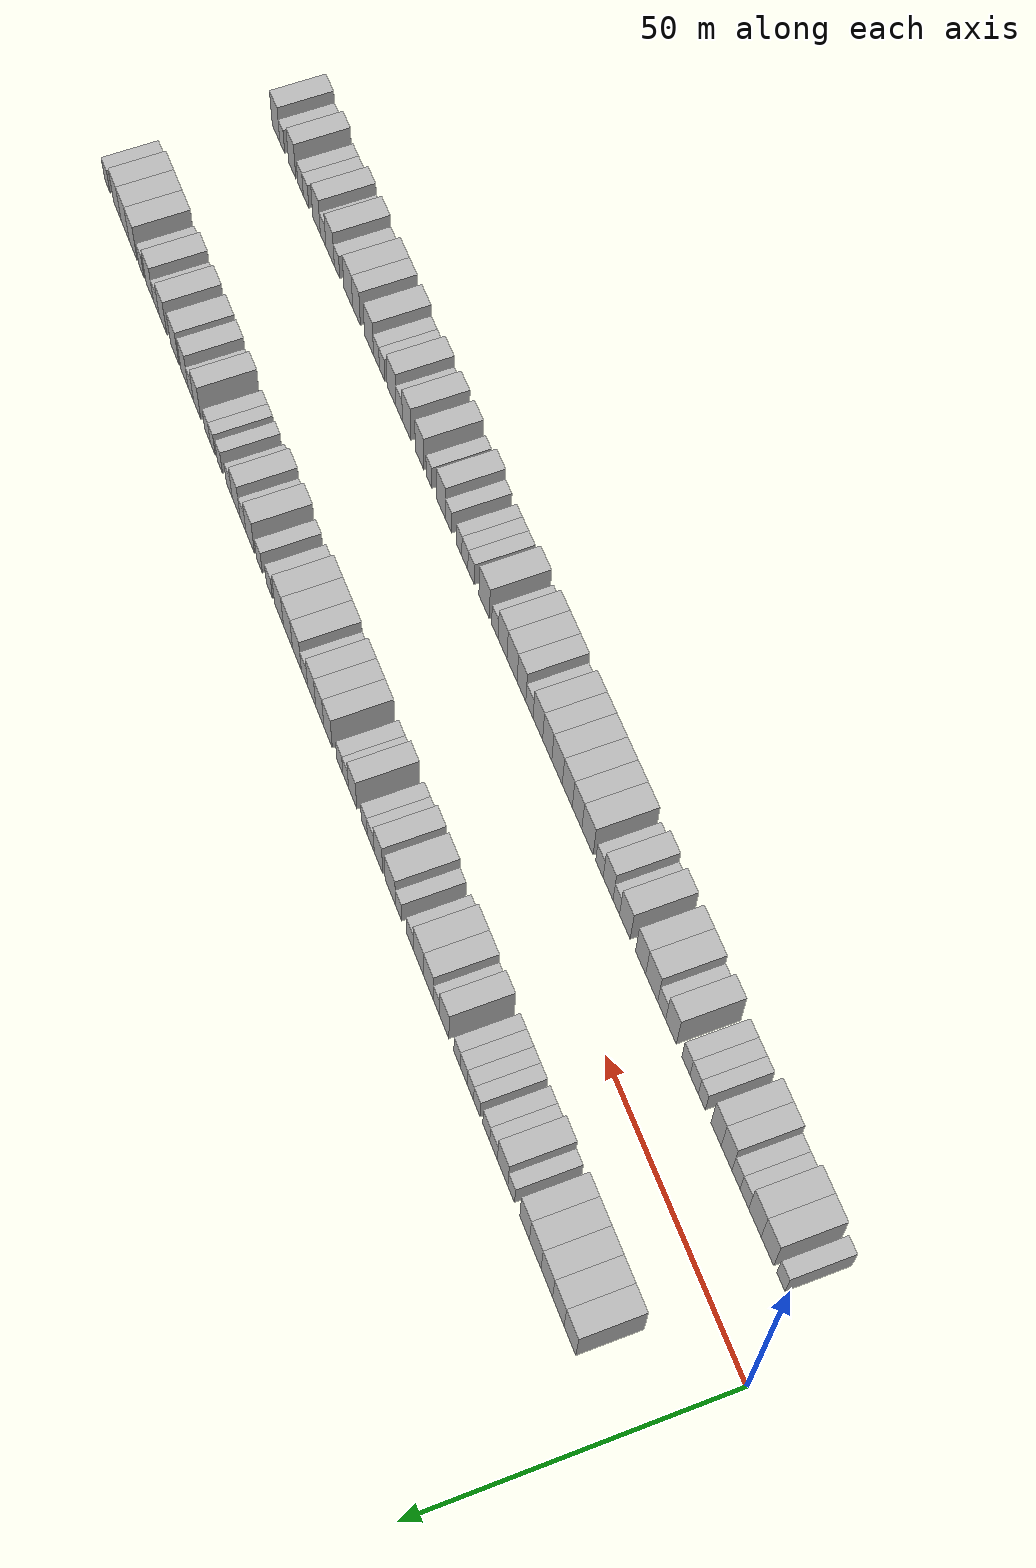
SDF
<sdf version="1.6">
 <world name="default">
  <scene>
   <sky><clouds><speed>12</speed></clouds></sky>
   <ambient>0.4 0.4 0.4 1</ambient>
   <background>0.7 0.7 0.7 1</background>
   <shadows>1</shadows>
  </scene>
  <gravity>0 0 -9.8066</gravity>
  <magnetic_field>6e-06 2.3e-05 -4.2e-05</magnetic_field>
  <physics default="0" name="default_physics" type="ode">
   <ode>
    <solver>
     <type>quick</type>
     <iters>10</iters>
     <sor>1.0</sor>
     <use_dynamic_moi_rescaling>0</use_dynamic_moi_rescaling>
    </solver>
    <constraints>
     <cfm>0</cfm>
     <erp>0.2</erp>
     <contact_max_correcting_vel>100</contact_max_correcting_vel>
     <contact_surface_layer>0.001</contact_surface_layer>
    </constraints>
   </ode>
   <max_step_size>0.004</max_step_size>
   <real_time_factor>1</real_time_factor>
   <real_time_update_rate>250</real_time_update_rate>
  </physics>
  <light name="sun" type="directional">
   <pose>0 0 10 0 0 0</pose>
   <diffuse>0.8 0.8 0.8 1</diffuse>
   <specular>0.2 0.2 0.2 1</specular>
   <attenuation>
    <range>1000</range>
    <constant>0.9</constant>
    <linear>0.01</linear>
    <quadratic>0.001</quadratic>
   </attenuation>
   <direction>-0.5 0.1 -0.9</direction>
  </light>
  <model name="building_1">
   <static>1</static>
   <pose>14.1433 15.0000 0 0.000000 0.000000 1.570796</pose>
   <link name="link">
    <pose>0 0 4.50 0 0 0</pose>
    <collision name="collision"><geometry><box><size>10.0000 4.2866 9.0000</size></box></geometry></collision>
    <visual name="visual">
     <cast_shadows>0</cast_shadows>
     <geometry><box><size>10.0000 4.2866 9.0000</size></box></geometry>
     <material>
      <script>
       <uri>model://HANNAS_wall/materials/scripts</uri>
       <uri>model://HANNAS_wall/materials/textures</uri>
       <name>vrc/HANNAS_wall</name>
      </script>
     </material>
    </visual>
   </link>
  </model>
  <model name="building_2">
   <static>1</static>
   <pose>18.3812 15.0000 0 0.000000 0.000000 1.570796</pose>
   <link name="link">
    <pose>0 0 4.50 0 0 0</pose>
    <collision name="collision"><geometry><box><size>10.0000 4.1893 9.0000</size></box></geometry></collision>
    <visual name="visual">
     <cast_shadows>0</cast_shadows>
     <geometry><box><size>10.0000 4.1893 9.0000</size></box></geometry>
     <material>
      <script>
       <uri>model://HANNAS_wall/materials/scripts</uri>
       <uri>model://HANNAS_wall/materials/textures</uri>
       <name>vrc/HANNAS_wall</name>
      </script>
     </material>
    </visual>
   </link>
  </model>
  <model name="building_3">
   <static>1</static>
   <pose>22.5935 15.0000 0 0.000000 0.000000 1.570796</pose>
   <link name="link">
    <pose>0 0 4.50 0 0 0</pose>
    <collision name="collision"><geometry><box><size>10.0000 4.2353 9.0000</size></box></geometry></collision>
    <visual name="visual">
     <cast_shadows>0</cast_shadows>
     <geometry><box><size>10.0000 4.2353 9.0000</size></box></geometry>
     <material>
      <script>
       <uri>model://HANNAS_wall/materials/scripts</uri>
       <uri>model://HANNAS_wall/materials/textures</uri>
       <name>vrc/HANNAS_wall</name>
      </script>
     </material>
    </visual>
   </link>
  </model>
  <model name="building_4">
   <static>1</static>
   <pose>26.8650 15.0000 0 0.000000 0.000000 1.570796</pose>
   <link name="link">
    <pose>0 0 4.50 0 0 0</pose>
    <collision name="collision"><geometry><box><size>10.0000 4.3076 9.0000</size></box></geometry></collision>
    <visual name="visual">
     <cast_shadows>0</cast_shadows>
     <geometry><box><size>10.0000 4.3076 9.0000</size></box></geometry>
     <material>
      <script>
       <uri>model://HANNAS_wall/materials/scripts</uri>
       <uri>model://HANNAS_wall/materials/textures</uri>
       <name>vrc/HANNAS_wall</name>
      </script>
     </material>
    </visual>
   </link>
  </model>
  <model name="building_5">
   <static>1</static>
   <pose>30.8387 15.0000 0 0.000000 0.000000 1.570796</pose>
   <link name="link">
    <pose>0 0 4.50 0 0 0</pose>
    <collision name="collision"><geometry><box><size>10.0000 3.6397 9.0000</size></box></geometry></collision>
    <visual name="visual">
     <cast_shadows>0</cast_shadows>
     <geometry><box><size>10.0000 3.6397 9.0000</size></box></geometry>
     <material>
      <script>
       <uri>model://HANNAS_wall/materials/scripts</uri>
       <uri>model://HANNAS_wall/materials/textures</uri>
       <name>vrc/HANNAS_wall</name>
      </script>
     </material>
    </visual>
   </link>
  </model>
  <model name="building_6">
   <static>1</static>
   <pose>35.9202 15.0000 0 0.000000 0.000000 1.570796</pose>
   <link name="link">
    <pose>0 0 3.00 0 0 0</pose>
    <collision name="collision"><geometry><box><size>10.0000 2.5234 6.0000</size></box></geometry></collision>
    <visual name="visual">
     <cast_shadows>0</cast_shadows>
     <geometry><box><size>10.0000 2.5234 6.0000</size></box></geometry>
     <material>
      <script>
       <uri>model://HANNAS_wall/materials/scripts</uri>
       <uri>model://HANNAS_wall/materials/textures</uri>
       <name>vrc/HANNAS_wall</name>
      </script>
     </material>
    </visual>
   </link>
  </model>
  <model name="building_7">
   <static>1</static>
   <pose>39.1829 15.0000 0 0.000000 0.000000 1.570796</pose>
   <link name="link">
    <pose>0 0 4.50 0 0 0</pose>
    <collision name="collision"><geometry><box><size>10.0000 4.0020 9.0000</size></box></geometry></collision>
    <visual name="visual">
     <cast_shadows>0</cast_shadows>
     <geometry><box><size>10.0000 4.0020 9.0000</size></box></geometry>
     <material>
      <script>
       <uri>model://HANNAS_wall/materials/scripts</uri>
       <uri>model://HANNAS_wall/materials/textures</uri>
       <name>vrc/HANNAS_wall</name>
      </script>
     </material>
    </visual>
   </link>
  </model>
  <model name="building_8">
   <static>1</static>
   <pose>42.6572 15.0000 0 0.000000 0.000000 1.570796</pose>
   <link name="link">
    <pose>0 0 3.00 0 0 0</pose>
    <collision name="collision"><geometry><box><size>10.0000 2.9467 6.0000</size></box></geometry></collision>
    <visual name="visual">
     <cast_shadows>0</cast_shadows>
     <geometry><box><size>10.0000 2.9467 6.0000</size></box></geometry>
     <material>
      <script>
       <uri>model://HANNAS_wall/materials/scripts</uri>
       <uri>model://HANNAS_wall/materials/textures</uri>
       <name>vrc/HANNAS_wall</name>
      </script>
     </material>
    </visual>
   </link>
  </model>
  <model name="building_9">
   <static>1</static>
   <pose>45.4963 15.0000 0 0.000000 0.000000 1.570796</pose>
   <link name="link">
    <pose>0 0 3.00 0 0 0</pose>
    <collision name="collision"><geometry><box><size>10.0000 2.7314 6.0000</size></box></geometry></collision>
    <visual name="visual">
     <cast_shadows>0</cast_shadows>
     <geometry><box><size>10.0000 2.7314 6.0000</size></box></geometry>
     <material>
      <script>
       <uri>model://HANNAS_wall/materials/scripts</uri>
       <uri>model://HANNAS_wall/materials/textures</uri>
       <name>vrc/HANNAS_wall</name>
      </script>
     </material>
    </visual>
   </link>
  </model>
  <model name="building_10">
   <static>1</static>
   <pose>49.1422 15.0000 0 0.000000 0.000000 1.570796</pose>
   <link name="link">
    <pose>0 0 3.00 0 0 0</pose>
    <collision name="collision"><geometry><box><size>10.0000 2.5605 6.0000</size></box></geometry></collision>
    <visual name="visual">
     <cast_shadows>0</cast_shadows>
     <geometry><box><size>10.0000 2.5605 6.0000</size></box></geometry>
     <material>
      <script>
       <uri>model://HANNAS_wall/materials/scripts</uri>
       <uri>model://HANNAS_wall/materials/textures</uri>
       <name>vrc/HANNAS_wall</name>
      </script>
     </material>
    </visual>
   </link>
  </model>
  <model name="building_11">
   <static>1</static>
   <pose>51.7119 15.0000 0 0.000000 0.000000 1.570796</pose>
   <link name="link">
    <pose>0 0 3.00 0 0 0</pose>
    <collision name="collision"><geometry><box><size>10.0000 2.5790 6.0000</size></box></geometry></collision>
    <visual name="visual">
     <cast_shadows>0</cast_shadows>
     <geometry><box><size>10.0000 2.5790 6.0000</size></box></geometry>
     <material>
      <script>
       <uri>model://HANNAS_wall/materials/scripts</uri>
       <uri>model://HANNAS_wall/materials/textures</uri>
       <name>vrc/HANNAS_wall</name>
      </script>
     </material>
    </visual>
   </link>
  </model>
  <model name="building_12">
   <static>1</static>
   <pose>54.3860 15.0000 0 0.000000 0.000000 1.570796</pose>
   <link name="link">
    <pose>0 0 3.00 0 0 0</pose>
    <collision name="collision"><geometry><box><size>10.0000 2.7691 6.0000</size></box></geometry></collision>
    <visual name="visual">
     <cast_shadows>0</cast_shadows>
     <geometry><box><size>10.0000 2.7691 6.0000</size></box></geometry>
     <material>
      <script>
       <uri>model://HANNAS_wall/materials/scripts</uri>
       <uri>model://HANNAS_wall/materials/textures</uri>
       <name>vrc/HANNAS_wall</name>
      </script>
     </material>
    </visual>
   </link>
  </model>
  <model name="building_13">
   <static>1</static>
   <pose>57.0139 15.0000 0 0.000000 0.000000 1.570796</pose>
   <link name="link">
    <pose>0 0 3.00 0 0 0</pose>
    <collision name="collision"><geometry><box><size>10.0000 2.4868 6.0000</size></box></geometry></collision>
    <visual name="visual">
     <cast_shadows>0</cast_shadows>
     <geometry><box><size>10.0000 2.4868 6.0000</size></box></geometry>
     <material>
      <script>
       <uri>model://HANNAS_wall/materials/scripts</uri>
       <uri>model://HANNAS_wall/materials/textures</uri>
       <name>vrc/HANNAS_wall</name>
      </script>
     </material>
    </visual>
   </link>
  </model>
  <model name="building_14">
   <static>1</static>
   <pose>62.0946 15.0000 0 0.000000 0.000000 1.570796</pose>
   <link name="link">
    <pose>0 0 4.50 0 0 0</pose>
    <collision name="collision"><geometry><box><size>10.0000 3.6747 9.0000</size></box></geometry></collision>
    <visual name="visual">
     <cast_shadows>0</cast_shadows>
     <geometry><box><size>10.0000 3.6747 9.0000</size></box></geometry>
     <material>
      <script>
       <uri>model://HANNAS_wall/materials/scripts</uri>
       <uri>model://HANNAS_wall/materials/textures</uri>
       <name>vrc/HANNAS_wall</name>
      </script>
     </material>
    </visual>
   </link>
  </model>
  <model name="building_15">
   <static>1</static>
   <pose>65.1895 15.0000 0 0.000000 0.000000 1.570796</pose>
   <link name="link">
    <pose>0 0 3.00 0 0 0</pose>
    <collision name="collision"><geometry><box><size>10.0000 2.5151 6.0000</size></box></geometry></collision>
    <visual name="visual">
     <cast_shadows>0</cast_shadows>
     <geometry><box><size>10.0000 2.5151 6.0000</size></box></geometry>
     <material>
      <script>
       <uri>model://HANNAS_wall/materials/scripts</uri>
       <uri>model://HANNAS_wall/materials/textures</uri>
       <name>vrc/HANNAS_wall</name>
      </script>
     </material>
    </visual>
   </link>
  </model>
  <model name="building_16">
   <static>1</static>
   <pose>68.4266 15.0000 0 0.000000 0.000000 1.570796</pose>
   <link name="link">
    <pose>0 0 4.50 0 0 0</pose>
    <collision name="collision"><geometry><box><size>10.0000 3.9590 9.0000</size></box></geometry></collision>
    <visual name="visual">
     <cast_shadows>0</cast_shadows>
     <geometry><box><size>10.0000 3.9590 9.0000</size></box></geometry>
     <material>
      <script>
       <uri>model://HANNAS_wall/materials/scripts</uri>
       <uri>model://HANNAS_wall/materials/textures</uri>
       <name>vrc/HANNAS_wall</name>
      </script>
     </material>
    </visual>
   </link>
  </model>
  <model name="building_17">
   <static>1</static>
   <pose>72.5462 15.0000 0 0.000000 0.000000 1.570796</pose>
   <link name="link">
    <pose>0 0 4.50 0 0 0</pose>
    <collision name="collision"><geometry><box><size>10.0000 4.2803 9.0000</size></box></geometry></collision>
    <visual name="visual">
     <cast_shadows>0</cast_shadows>
     <geometry><box><size>10.0000 4.2803 9.0000</size></box></geometry>
     <material>
      <script>
       <uri>model://HANNAS_wall/materials/scripts</uri>
       <uri>model://HANNAS_wall/materials/textures</uri>
       <name>vrc/HANNAS_wall</name>
      </script>
     </material>
    </visual>
   </link>
  </model>
  <model name="building_18">
   <static>1</static>
   <pose>76.1411 15.0000 0 0.000000 0.000000 1.570796</pose>
   <link name="link">
    <pose>0 0 3.00 0 0 0</pose>
    <collision name="collision"><geometry><box><size>10.0000 2.9094 6.0000</size></box></geometry></collision>
    <visual name="visual">
     <cast_shadows>0</cast_shadows>
     <geometry><box><size>10.0000 2.9094 6.0000</size></box></geometry>
     <material>
      <script>
       <uri>model://HANNAS_wall/materials/scripts</uri>
       <uri>model://HANNAS_wall/materials/textures</uri>
       <name>vrc/HANNAS_wall</name>
      </script>
     </material>
    </visual>
   </link>
  </model>
  <model name="building_19">
   <static>1</static>
   <pose>80.8462 15.0000 0 0.000000 0.000000 1.570796</pose>
   <link name="link">
    <pose>0 0 3.00 0 0 0</pose>
    <collision name="collision"><geometry><box><size>10.0000 2.5008 6.0000</size></box></geometry></collision>
    <visual name="visual">
     <cast_shadows>0</cast_shadows>
     <geometry><box><size>10.0000 2.5008 6.0000</size></box></geometry>
     <material>
      <script>
       <uri>model://HANNAS_wall/materials/scripts</uri>
       <uri>model://HANNAS_wall/materials/textures</uri>
       <name>vrc/HANNAS_wall</name>
      </script>
     </material>
    </visual>
   </link>
  </model>
  <model name="building_20">
   <static>1</static>
   <pose>84.3462 15.0000 0 0.000000 0.000000 1.570796</pose>
   <link name="link">
    <pose>0 0 4.50 0 0 0</pose>
    <collision name="collision"><geometry><box><size>10.0000 4.4993 9.0000</size></box></geometry></collision>
    <visual name="visual">
     <cast_shadows>0</cast_shadows>
     <geometry><box><size>10.0000 4.4993 9.0000</size></box></geometry>
     <material>
      <script>
       <uri>model://HANNAS_wall/materials/scripts</uri>
       <uri>model://HANNAS_wall/materials/textures</uri>
       <name>vrc/HANNAS_wall</name>
      </script>
     </material>
    </visual>
   </link>
  </model>
  <model name="building_21">
   <static>1</static>
   <pose>89.4073 15.0000 0 0.000000 0.000000 1.570796</pose>
   <link name="link">
    <pose>0 0 4.50 0 0 0</pose>
    <collision name="collision"><geometry><box><size>10.0000 3.6229 9.0000</size></box></geometry></collision>
    <visual name="visual">
     <cast_shadows>0</cast_shadows>
     <geometry><box><size>10.0000 3.6229 9.0000</size></box></geometry>
     <material>
      <script>
       <uri>model://HANNAS_wall/materials/scripts</uri>
       <uri>model://HANNAS_wall/materials/textures</uri>
       <name>vrc/HANNAS_wall</name>
      </script>
     </material>
    </visual>
   </link>
  </model>
  <model name="building_22">
   <static>1</static>
   <pose>92.6987 15.0000 0 0.000000 0.000000 1.570796</pose>
   <link name="link">
    <pose>0 0 3.00 0 0 0</pose>
    <collision name="collision"><geometry><box><size>10.0000 2.9599 6.0000</size></box></geometry></collision>
    <visual name="visual">
     <cast_shadows>0</cast_shadows>
     <geometry><box><size>10.0000 2.9599 6.0000</size></box></geometry>
     <material>
      <script>
       <uri>model://HANNAS_wall/materials/scripts</uri>
       <uri>model://HANNAS_wall/materials/textures</uri>
       <name>vrc/HANNAS_wall</name>
      </script>
     </material>
    </visual>
   </link>
  </model>
  <model name="building_23">
   <static>1</static>
   <pose>95.4585 15.0000 0 0.000000 0.000000 1.570796</pose>
   <link name="link">
    <pose>0 0 3.00 0 0 0</pose>
    <collision name="collision"><geometry><box><size>10.0000 2.5597 6.0000</size></box></geometry></collision>
    <visual name="visual">
     <cast_shadows>0</cast_shadows>
     <geometry><box><size>10.0000 2.5597 6.0000</size></box></geometry>
     <material>
      <script>
       <uri>model://HANNAS_wall/materials/scripts</uri>
       <uri>model://HANNAS_wall/materials/textures</uri>
       <name>vrc/HANNAS_wall</name>
      </script>
     </material>
    </visual>
   </link>
  </model>
  <model name="building_24">
   <static>1</static>
   <pose>100.5434 15.0000 0 0.000000 0.000000 1.570796</pose>
   <link name="link">
    <pose>0 0 4.50 0 0 0</pose>
    <collision name="collision"><geometry><box><size>10.0000 3.6101 9.0000</size></box></geometry></collision>
    <visual name="visual">
     <cast_shadows>0</cast_shadows>
     <geometry><box><size>10.0000 3.6101 9.0000</size></box></geometry>
     <material>
      <script>
       <uri>model://HANNAS_wall/materials/scripts</uri>
       <uri>model://HANNAS_wall/materials/textures</uri>
       <name>vrc/HANNAS_wall</name>
      </script>
     </material>
    </visual>
   </link>
  </model>
  <model name="building_25">
   <static>1</static>
   <pose>103.5877 15.0000 0 0.000000 0.000000 1.570796</pose>
   <link name="link">
    <pose>0 0 3.00 0 0 0</pose>
    <collision name="collision"><geometry><box><size>10.0000 2.4786 6.0000</size></box></geometry></collision>
    <visual name="visual">
     <cast_shadows>0</cast_shadows>
     <geometry><box><size>10.0000 2.4786 6.0000</size></box></geometry>
     <material>
      <script>
       <uri>model://HANNAS_wall/materials/scripts</uri>
       <uri>model://HANNAS_wall/materials/textures</uri>
       <name>vrc/HANNAS_wall</name>
      </script>
     </material>
    </visual>
   </link>
  </model>
  <model name="building_26">
   <static>1</static>
   <pose>106.1811 15.0000 0 0.000000 0.000000 1.570796</pose>
   <link name="link">
    <pose>0 0 3.00 0 0 0</pose>
    <collision name="collision"><geometry><box><size>10.0000 2.7080 6.0000</size></box></geometry></collision>
    <visual name="visual">
     <cast_shadows>0</cast_shadows>
     <geometry><box><size>10.0000 2.7080 6.0000</size></box></geometry>
     <material>
      <script>
       <uri>model://HANNAS_wall/materials/scripts</uri>
       <uri>model://HANNAS_wall/materials/textures</uri>
       <name>vrc/HANNAS_wall</name>
      </script>
     </material>
    </visual>
   </link>
  </model>
  <model name="building_27">
   <static>1</static>
   <pose>111.4133 15.0000 0 0.000000 0.000000 1.570796</pose>
   <link name="link">
    <pose>0 0 4.50 0 0 0</pose>
    <collision name="collision"><geometry><box><size>10.0000 3.7564 9.0000</size></box></geometry></collision>
    <visual name="visual">
     <cast_shadows>0</cast_shadows>
     <geometry><box><size>10.0000 3.7564 9.0000</size></box></geometry>
     <material>
      <script>
       <uri>model://HANNAS_wall/materials/scripts</uri>
       <uri>model://HANNAS_wall/materials/textures</uri>
       <name>vrc/HANNAS_wall</name>
      </script>
     </material>
    </visual>
   </link>
  </model>
  <model name="building_28">
   <static>1</static>
   <pose>115.1273 15.0000 0 0.000000 0.000000 1.570796</pose>
   <link name="link">
    <pose>0 0 4.50 0 0 0</pose>
    <collision name="collision"><geometry><box><size>10.0000 3.6715 9.0000</size></box></geometry></collision>
    <visual name="visual">
     <cast_shadows>0</cast_shadows>
     <geometry><box><size>10.0000 3.6715 9.0000</size></box></geometry>
     <material>
      <script>
       <uri>model://HANNAS_wall/materials/scripts</uri>
       <uri>model://HANNAS_wall/materials/textures</uri>
       <name>vrc/HANNAS_wall</name>
      </script>
     </material>
    </visual>
   </link>
  </model>
  <model name="building_29">
   <static>1</static>
   <pose>118.7872 15.0000 0 0.000000 0.000000 1.570796</pose>
   <link name="link">
    <pose>0 0 4.50 0 0 0</pose>
    <collision name="collision"><geometry><box><size>10.0000 3.6483 9.0000</size></box></geometry></collision>
    <visual name="visual">
     <cast_shadows>0</cast_shadows>
     <geometry><box><size>10.0000 3.6483 9.0000</size></box></geometry>
     <material>
      <script>
       <uri>model://HANNAS_wall/materials/scripts</uri>
       <uri>model://HANNAS_wall/materials/textures</uri>
       <name>vrc/HANNAS_wall</name>
      </script>
     </material>
    </visual>
   </link>
  </model>
  <model name="building_30">
   <static>1</static>
   <pose>122.0579 15.0000 0 0.000000 0.000000 1.570796</pose>
   <link name="link">
    <pose>0 0 3.00 0 0 0</pose>
    <collision name="collision"><geometry><box><size>10.0000 2.8931 6.0000</size></box></geometry></collision>
    <visual name="visual">
     <cast_shadows>0</cast_shadows>
     <geometry><box><size>10.0000 2.8931 6.0000</size></box></geometry>
     <material>
      <script>
       <uri>model://HANNAS_wall/materials/scripts</uri>
       <uri>model://HANNAS_wall/materials/textures</uri>
       <name>vrc/HANNAS_wall</name>
      </script>
     </material>
    </visual>
   </link>
  </model>
  <model name="building_31">
   <static>1</static>
   <pose>125.5207 15.0000 0 0.000000 0.000000 1.570796</pose>
   <link name="link">
    <pose>0 0 4.50 0 0 0</pose>
    <collision name="collision"><geometry><box><size>10.0000 4.0324 9.0000</size></box></geometry></collision>
    <visual name="visual">
     <cast_shadows>0</cast_shadows>
     <geometry><box><size>10.0000 4.0324 9.0000</size></box></geometry>
     <material>
      <script>
       <uri>model://HANNAS_wall/materials/scripts</uri>
       <uri>model://HANNAS_wall/materials/textures</uri>
       <name>vrc/HANNAS_wall</name>
      </script>
     </material>
    </visual>
   </link>
  </model>
  <model name="building_32">
   <static>1</static>
   <pose>129.6454 15.0000 0 0.000000 0.000000 1.570796</pose>
   <link name="link">
    <pose>0 0 4.50 0 0 0</pose>
    <collision name="collision"><geometry><box><size>10.0000 4.2172 9.0000</size></box></geometry></collision>
    <visual name="visual">
     <cast_shadows>0</cast_shadows>
     <geometry><box><size>10.0000 4.2172 9.0000</size></box></geometry>
     <material>
      <script>
       <uri>model://HANNAS_wall/materials/scripts</uri>
       <uri>model://HANNAS_wall/materials/textures</uri>
       <name>vrc/HANNAS_wall</name>
      </script>
     </material>
    </visual>
   </link>
  </model>
  <model name="building_33">
   <static>1</static>
   <pose>133.8189 15.0000 0 0.000000 0.000000 1.570796</pose>
   <link name="link">
    <pose>0 0 4.50 0 0 0</pose>
    <collision name="collision"><geometry><box><size>10.0000 4.1298 9.0000</size></box></geometry></collision>
    <visual name="visual">
     <cast_shadows>0</cast_shadows>
     <geometry><box><size>10.0000 4.1298 9.0000</size></box></geometry>
     <material>
      <script>
       <uri>model://HANNAS_wall/materials/scripts</uri>
       <uri>model://HANNAS_wall/materials/textures</uri>
       <name>vrc/HANNAS_wall</name>
      </script>
     </material>
    </visual>
   </link>
  </model>
  <model name="building_34">
   <static>1</static>
   <pose>138.3126 15.0000 0 0.000000 0.000000 1.570796</pose>
   <link name="link">
    <pose>0 0 3.00 0 0 0</pose>
    <collision name="collision"><geometry><box><size>10.0000 2.8577 6.0000</size></box></geometry></collision>
    <visual name="visual">
     <cast_shadows>0</cast_shadows>
     <geometry><box><size>10.0000 2.8577 6.0000</size></box></geometry>
     <material>
      <script>
       <uri>model://HANNAS_wall/materials/scripts</uri>
       <uri>model://HANNAS_wall/materials/textures</uri>
       <name>vrc/HANNAS_wall</name>
      </script>
     </material>
    </visual>
   </link>
  </model>
  <model name="building_35">
   <static>1</static>
   <pose>143.1070 15.0000 0 0.000000 0.000000 1.570796</pose>
   <link name="link">
    <pose>0 0 3.00 0 0 0</pose>
    <collision name="collision"><geometry><box><size>10.0000 2.7310 6.0000</size></box></geometry></collision>
    <visual name="visual">
     <cast_shadows>0</cast_shadows>
     <geometry><box><size>10.0000 2.7310 6.0000</size></box></geometry>
     <material>
      <script>
       <uri>model://HANNAS_wall/materials/scripts</uri>
       <uri>model://HANNAS_wall/materials/textures</uri>
       <name>vrc/HANNAS_wall</name>
      </script>
     </material>
    </visual>
   </link>
  </model>
  <model name="building_36">
   <static>1</static>
   <pose>147.5088 15.0000 0 0.000000 0.000000 1.570796</pose>
   <link name="link">
    <pose>0 0 4.50 0 0 0</pose>
    <collision name="collision"><geometry><box><size>10.0000 4.0727 9.0000</size></box></geometry></collision>
    <visual name="visual">
     <cast_shadows>0</cast_shadows>
     <geometry><box><size>10.0000 4.0727 9.0000</size></box></geometry>
     <material>
      <script>
       <uri>model://HANNAS_wall/materials/scripts</uri>
       <uri>model://HANNAS_wall/materials/textures</uri>
       <name>vrc/HANNAS_wall</name>
      </script>
     </material>
    </visual>
   </link>
  </model>
  <model name="building_37">
   <static>1</static>
   <pose>150.9793 15.0000 0 0.000000 0.000000 1.570796</pose>
   <link name="link">
    <pose>0 0 3.00 0 0 0</pose>
    <collision name="collision"><geometry><box><size>10.0000 2.8682 6.0000</size></box></geometry></collision>
    <visual name="visual">
     <cast_shadows>0</cast_shadows>
     <geometry><box><size>10.0000 2.8682 6.0000</size></box></geometry>
     <material>
      <script>
       <uri>model://HANNAS_wall/materials/scripts</uri>
       <uri>model://HANNAS_wall/materials/textures</uri>
       <name>vrc/HANNAS_wall</name>
      </script>
     </material>
    </visual>
   </link>
  </model>
  <model name="building_38">
   <static>1</static>
   <pose>154.3399 15.0000 0 0.000000 0.000000 1.570796</pose>
   <link name="link">
    <pose>0 0 4.50 0 0 0</pose>
    <collision name="collision"><geometry><box><size>10.0000 3.8530 9.0000</size></box></geometry></collision>
    <visual name="visual">
     <cast_shadows>0</cast_shadows>
     <geometry><box><size>10.0000 3.8530 9.0000</size></box></geometry>
     <material>
      <script>
       <uri>model://HANNAS_wall/materials/scripts</uri>
       <uri>model://HANNAS_wall/materials/textures</uri>
       <name>vrc/HANNAS_wall</name>
      </script>
     </material>
    </visual>
   </link>
  </model>
  <model name="building_39">
   <static>1</static>
   <pose>157.6672 15.0000 0 0.000000 0.000000 1.570796</pose>
   <link name="link">
    <pose>0 0 3.00 0 0 0</pose>
    <collision name="collision"><geometry><box><size>10.0000 2.8016 6.0000</size></box></geometry></collision>
    <visual name="visual">
     <cast_shadows>0</cast_shadows>
     <geometry><box><size>10.0000 2.8016 6.0000</size></box></geometry>
     <material>
      <script>
       <uri>model://HANNAS_wall/materials/scripts</uri>
       <uri>model://HANNAS_wall/materials/textures</uri>
       <name>vrc/HANNAS_wall</name>
      </script>
     </material>
    </visual>
   </link>
  </model>
  <model name="building_40">
   <static>1</static>
   <pose>162.3288 15.0000 0 0.000000 0.000000 1.570796</pose>
   <link name="link">
    <pose>0 0 3.00 0 0 0</pose>
    <collision name="collision"><geometry><box><size>10.0000 2.5216 6.0000</size></box></geometry></collision>
    <visual name="visual">
     <cast_shadows>0</cast_shadows>
     <geometry><box><size>10.0000 2.5216 6.0000</size></box></geometry>
     <material>
      <script>
       <uri>model://HANNAS_wall/materials/scripts</uri>
       <uri>model://HANNAS_wall/materials/textures</uri>
       <name>vrc/HANNAS_wall</name>
      </script>
     </material>
    </visual>
   </link>
  </model>
  <model name="building_41">
   <static>1</static>
   <pose>165.8322 15.0000 0 0.000000 0.000000 1.570796</pose>
   <link name="link">
    <pose>0 0 3.00 0 0 0</pose>
    <collision name="collision"><geometry><box><size>10.0000 2.4854 6.0000</size></box></geometry></collision>
    <visual name="visual">
     <cast_shadows>0</cast_shadows>
     <geometry><box><size>10.0000 2.4854 6.0000</size></box></geometry>
     <material>
      <script>
       <uri>model://HANNAS_wall/materials/scripts</uri>
       <uri>model://HANNAS_wall/materials/textures</uri>
       <name>vrc/HANNAS_wall</name>
      </script>
     </material>
    </visual>
   </link>
  </model>
  <model name="building_42">
   <static>1</static>
   <pose>168.4433 15.0000 0 0.000000 0.000000 1.570796</pose>
   <link name="link">
    <pose>0 0 3.00 0 0 0</pose>
    <collision name="collision"><geometry><box><size>10.0000 2.7369 6.0000</size></box></geometry></collision>
    <visual name="visual">
     <cast_shadows>0</cast_shadows>
     <geometry><box><size>10.0000 2.7369 6.0000</size></box></geometry>
     <material>
      <script>
       <uri>model://HANNAS_wall/materials/scripts</uri>
       <uri>model://HANNAS_wall/materials/textures</uri>
       <name>vrc/HANNAS_wall</name>
      </script>
     </material>
    </visual>
   </link>
  </model>
  <model name="building_43">
   <static>1</static>
   <pose>173.6424 15.0000 0 0.000000 0.000000 1.570796</pose>
   <link name="link">
    <pose>0 0 4.50 0 0 0</pose>
    <collision name="collision"><geometry><box><size>10.0000 3.6613 9.0000</size></box></geometry></collision>
    <visual name="visual">
     <cast_shadows>0</cast_shadows>
     <geometry><box><size>10.0000 3.6613 9.0000</size></box></geometry>
     <material>
      <script>
       <uri>model://HANNAS_wall/materials/scripts</uri>
       <uri>model://HANNAS_wall/materials/textures</uri>
       <name>vrc/HANNAS_wall</name>
      </script>
     </material>
    </visual>
   </link>
  </model>
  <model name="building_44">
   <static>1</static>
   <pose>176.8333 15.0000 0 0.000000 0.000000 1.570796</pose>
   <link name="link">
    <pose>0 0 3.00 0 0 0</pose>
    <collision name="collision"><geometry><box><size>10.0000 2.7204 6.0000</size></box></geometry></collision>
    <visual name="visual">
     <cast_shadows>0</cast_shadows>
     <geometry><box><size>10.0000 2.7204 6.0000</size></box></geometry>
     <material>
      <script>
       <uri>model://HANNAS_wall/materials/scripts</uri>
       <uri>model://HANNAS_wall/materials/textures</uri>
       <name>vrc/HANNAS_wall</name>
      </script>
     </material>
    </visual>
   </link>
  </model>
  <model name="building_45">
   <static>1</static>
   <pose>180.0384 15.0000 0 0.000000 0.000000 1.570796</pose>
   <link name="link">
    <pose>0 0 4.50 0 0 0</pose>
    <collision name="collision"><geometry><box><size>10.0000 3.6898 9.0000</size></box></geometry></collision>
    <visual name="visual">
     <cast_shadows>0</cast_shadows>
     <geometry><box><size>10.0000 3.6898 9.0000</size></box></geometry>
     <material>
      <script>
       <uri>model://HANNAS_wall/materials/scripts</uri>
       <uri>model://HANNAS_wall/materials/textures</uri>
       <name>vrc/HANNAS_wall</name>
      </script>
     </material>
    </visual>
   </link>
  </model>
  <model name="building_46">
   <static>1</static>
   <pose>185.0139 15.0000 0 0.000000 0.000000 1.570796</pose>
   <link name="link">
    <pose>0 0 4.50 0 0 0</pose>
    <collision name="collision"><geometry><box><size>10.0000 4.2611 9.0000</size></box></geometry></collision>
    <visual name="visual">
     <cast_shadows>0</cast_shadows>
     <geometry><box><size>10.0000 4.2611 9.0000</size></box></geometry>
     <material>
      <script>
       <uri>model://HANNAS_wall/materials/scripts</uri>
       <uri>model://HANNAS_wall/materials/textures</uri>
       <name>vrc/HANNAS_wall</name>
      </script>
     </material>
    </visual>
   </link>
  </model>
  <model name="building_47">
   <static>1</static>
   <pose>191.1745 15.0000 0 0.000000 0.000000 1.570796</pose>
   <link name="link">
    <pose>0 0 4.50 0 0 0</pose>
    <collision name="collision"><geometry><box><size>10.0000 4.0600 9.0000</size></box></geometry></collision>
    <visual name="visual">
     <cast_shadows>0</cast_shadows>
     <geometry><box><size>10.0000 4.0600 9.0000</size></box></geometry>
     <material>
      <script>
       <uri>model://HANNAS_wall/materials/scripts</uri>
       <uri>model://HANNAS_wall/materials/textures</uri>
       <name>vrc/HANNAS_wall</name>
      </script>
     </material>
    </visual>
   </link>
  </model>
  <model name="building_48">
   <static>1</static>
   <pose>194.7028 15.0000 0 0.000000 0.000000 1.570796</pose>
   <link name="link">
    <pose>0 0 3.00 0 0 0</pose>
    <collision name="collision"><geometry><box><size>10.0000 2.9967 6.0000</size></box></geometry></collision>
    <visual name="visual">
     <cast_shadows>0</cast_shadows>
     <geometry><box><size>10.0000 2.9967 6.0000</size></box></geometry>
     <material>
      <script>
       <uri>model://HANNAS_wall/materials/scripts</uri>
       <uri>model://HANNAS_wall/materials/textures</uri>
       <name>vrc/HANNAS_wall</name>
      </script>
     </material>
    </visual>
   </link>
  </model>
  <model name="building_49">
   <static>1</static>
   <pose>198.1769 15.0000 0 0.000000 0.000000 1.570796</pose>
   <link name="link">
    <pose>0 0 4.50 0 0 0</pose>
    <collision name="collision"><geometry><box><size>10.0000 3.9513 9.0000</size></box></geometry></collision>
    <visual name="visual">
     <cast_shadows>0</cast_shadows>
     <geometry><box><size>10.0000 3.9513 9.0000</size></box></geometry>
     <material>
      <script>
       <uri>model://HANNAS_wall/materials/scripts</uri>
       <uri>model://HANNAS_wall/materials/textures</uri>
       <name>vrc/HANNAS_wall</name>
      </script>
     </material>
    </visual>
   </link>
  </model>
  <model name="building_50">
   <static>1</static>
   <pose>202.5141 15.0000 0 0.000000 0.000000 1.570796</pose>
   <link name="link">
    <pose>0 0 3.00 0 0 0</pose>
    <collision name="collision"><geometry><box><size>10.0000 2.7232 6.0000</size></box></geometry></collision>
    <visual name="visual">
     <cast_shadows>0</cast_shadows>
     <geometry><box><size>10.0000 2.7232 6.0000</size></box></geometry>
     <material>
      <script>
       <uri>model://HANNAS_wall/materials/scripts</uri>
       <uri>model://HANNAS_wall/materials/textures</uri>
       <name>vrc/HANNAS_wall</name>
      </script>
     </material>
    </visual>
   </link>
  </model>
  <model name="building_51">
   <static>1</static>
   <pose>207.0337 15.0000 0 0.000000 0.000000 1.570796</pose>
   <link name="link">
    <pose>0 0 4.50 0 0 0</pose>
    <collision name="collision"><geometry><box><size>10.0000 4.3159 9.0000</size></box></geometry></collision>
    <visual name="visual">
     <cast_shadows>0</cast_shadows>
     <geometry><box><size>10.0000 4.3159 9.0000</size></box></geometry>
     <material>
      <script>
       <uri>model://HANNAS_wall/materials/scripts</uri>
       <uri>model://HANNAS_wall/materials/textures</uri>
       <name>vrc/HANNAS_wall</name>
      </script>
     </material>
    </visual>
   </link>
  </model>
  <model name="building_52">
   <static>1</static>
   <pose>211.3939 15.0000 0 0.000000 0.000000 1.570796</pose>
   <link name="link">
    <pose>0 0 4.50 0 0 0</pose>
    <collision name="collision"><geometry><box><size>10.0000 4.4045 9.0000</size></box></geometry></collision>
    <visual name="visual">
     <cast_shadows>0</cast_shadows>
     <geometry><box><size>10.0000 4.4045 9.0000</size></box></geometry>
     <material>
      <script>
       <uri>model://HANNAS_wall/materials/scripts</uri>
       <uri>model://HANNAS_wall/materials/textures</uri>
       <name>vrc/HANNAS_wall</name>
      </script>
     </material>
    </visual>
   </link>
  </model>
  <model name="building_53">
   <static>1</static>
   <pose>215.6306 15.0000 0 0.000000 0.000000 1.570796</pose>
   <link name="link">
    <pose>0 0 4.50 0 0 0</pose>
    <collision name="collision"><geometry><box><size>10.0000 4.0690 9.0000</size></box></geometry></collision>
    <visual name="visual">
     <cast_shadows>0</cast_shadows>
     <geometry><box><size>10.0000 4.0690 9.0000</size></box></geometry>
     <material>
      <script>
       <uri>model://HANNAS_wall/materials/scripts</uri>
       <uri>model://HANNAS_wall/materials/textures</uri>
       <name>vrc/HANNAS_wall</name>
      </script>
     </material>
    </visual>
   </link>
  </model>
  <model name="building_54">
   <static>1</static>
   <pose>221.0971 15.0000 0 0.000000 0.000000 1.570796</pose>
   <link name="link">
    <pose>0 0 3.00 0 0 0</pose>
    <collision name="collision"><geometry><box><size>10.0000 2.8641 6.0000</size></box></geometry></collision>
    <visual name="visual">
     <cast_shadows>0</cast_shadows>
     <geometry><box><size>10.0000 2.8641 6.0000</size></box></geometry>
     <material>
      <script>
       <uri>model://HANNAS_wall/materials/scripts</uri>
       <uri>model://HANNAS_wall/materials/textures</uri>
       <name>vrc/HANNAS_wall</name>
      </script>
     </material>
    </visual>
   </link>
  </model>
  <model name="building_55">
   <static>1</static>
   <pose>11.4036 -15.0000 0 0.000000 0.000000 1.570796</pose>
   <link name="link">
    <pose>0 0 3.00 0 0 0</pose>
    <collision name="collision"><geometry><box><size>10.0000 2.8072 6.0000</size></box></geometry></collision>
    <visual name="visual">
     <cast_shadows>0</cast_shadows>
     <geometry><box><size>10.0000 2.8072 6.0000</size></box></geometry>
     <material>
      <script>
       <uri>model://HANNAS_wall/materials/scripts</uri>
       <uri>model://HANNAS_wall/materials/textures</uri>
       <name>vrc/HANNAS_wall</name>
      </script>
     </material>
    </visual>
   </link>
  </model>
  <model name="building_56">
   <static>1</static>
   <pose>15.9590 -15.0000 0 0.000000 0.000000 1.570796</pose>
   <link name="link">
    <pose>0 0 4.50 0 0 0</pose>
    <collision name="collision"><geometry><box><size>10.0000 4.3037 9.0000</size></box></geometry></collision>
    <visual name="visual">
     <cast_shadows>0</cast_shadows>
     <geometry><box><size>10.0000 4.3037 9.0000</size></box></geometry>
     <material>
      <script>
       <uri>model://HANNAS_wall/materials/scripts</uri>
       <uri>model://HANNAS_wall/materials/textures</uri>
       <name>vrc/HANNAS_wall</name>
      </script>
     </material>
    </visual>
   </link>
  </model>
  <model name="building_57">
   <static>1</static>
   <pose>20.2456 -15.0000 0 0.000000 0.000000 1.570796</pose>
   <link name="link">
    <pose>0 0 4.50 0 0 0</pose>
    <collision name="collision"><geometry><box><size>10.0000 4.2694 9.0000</size></box></geometry></collision>
    <visual name="visual">
     <cast_shadows>0</cast_shadows>
     <geometry><box><size>10.0000 4.2694 9.0000</size></box></geometry>
     <material>
      <script>
       <uri>model://HANNAS_wall/materials/scripts</uri>
       <uri>model://HANNAS_wall/materials/textures</uri>
       <name>vrc/HANNAS_wall</name>
      </script>
     </material>
    </visual>
   </link>
  </model>
  <model name="building_58">
   <static>1</static>
   <pose>23.8735 -15.0000 0 0.000000 0.000000 1.570796</pose>
   <link name="link">
    <pose>0 0 3.00 0 0 0</pose>
    <collision name="collision"><geometry><box><size>10.0000 2.9865 6.0000</size></box></geometry></collision>
    <visual name="visual">
     <cast_shadows>0</cast_shadows>
     <geometry><box><size>10.0000 2.9865 6.0000</size></box></geometry>
     <material>
      <script>
       <uri>model://HANNAS_wall/materials/scripts</uri>
       <uri>model://HANNAS_wall/materials/textures</uri>
       <name>vrc/HANNAS_wall</name>
      </script>
     </material>
    </visual>
   </link>
  </model>
  <model name="building_59">
   <static>1</static>
   <pose>26.7877 -15.0000 0 0.000000 0.000000 1.570796</pose>
   <link name="link">
    <pose>0 0 3.00 0 0 0</pose>
    <collision name="collision"><geometry><box><size>10.0000 2.8418 6.0000</size></box></geometry></collision>
    <visual name="visual">
     <cast_shadows>0</cast_shadows>
     <geometry><box><size>10.0000 2.8418 6.0000</size></box></geometry>
     <material>
      <script>
       <uri>model://HANNAS_wall/materials/scripts</uri>
       <uri>model://HANNAS_wall/materials/textures</uri>
       <name>vrc/HANNAS_wall</name>
      </script>
     </material>
    </visual>
   </link>
  </model>
  <model name="building_60">
   <static>1</static>
   <pose>30.0855 -15.0000 0 0.000000 0.000000 1.570796</pose>
   <link name="link">
    <pose>0 0 4.50 0 0 0</pose>
    <collision name="collision"><geometry><box><size>10.0000 3.7539 9.0000</size></box></geometry></collision>
    <visual name="visual">
     <cast_shadows>0</cast_shadows>
     <geometry><box><size>10.0000 3.7539 9.0000</size></box></geometry>
     <material>
      <script>
       <uri>model://HANNAS_wall/materials/scripts</uri>
       <uri>model://HANNAS_wall/materials/textures</uri>
       <name>vrc/HANNAS_wall</name>
      </script>
     </material>
    </visual>
   </link>
  </model>
  <model name="building_61">
   <static>1</static>
   <pose>33.7828 -15.0000 0 0.000000 0.000000 1.570796</pose>
   <link name="link">
    <pose>0 0 4.50 0 0 0</pose>
    <collision name="collision"><geometry><box><size>10.0000 3.6406 9.0000</size></box></geometry></collision>
    <visual name="visual">
     <cast_shadows>0</cast_shadows>
     <geometry><box><size>10.0000 3.6406 9.0000</size></box></geometry>
     <material>
      <script>
       <uri>model://HANNAS_wall/materials/scripts</uri>
       <uri>model://HANNAS_wall/materials/textures</uri>
       <name>vrc/HANNAS_wall</name>
      </script>
     </material>
    </visual>
   </link>
  </model>
  <model name="building_62">
   <static>1</static>
   <pose>38.8738 -15.0000 0 0.000000 0.000000 1.570796</pose>
   <link name="link">
    <pose>0 0 3.00 0 0 0</pose>
    <collision name="collision"><geometry><box><size>10.0000 2.5413 6.0000</size></box></geometry></collision>
    <visual name="visual">
     <cast_shadows>0</cast_shadows>
     <geometry><box><size>10.0000 2.5413 6.0000</size></box></geometry>
     <material>
      <script>
       <uri>model://HANNAS_wall/materials/scripts</uri>
       <uri>model://HANNAS_wall/materials/textures</uri>
       <name>vrc/HANNAS_wall</name>
      </script>
     </material>
    </visual>
   </link>
  </model>
  <model name="building_63">
   <static>1</static>
   <pose>41.6143 -15.0000 0 0.000000 0.000000 1.570796</pose>
   <link name="link">
    <pose>0 0 3.00 0 0 0</pose>
    <collision name="collision"><geometry><box><size>10.0000 2.9398 6.0000</size></box></geometry></collision>
    <visual name="visual">
     <cast_shadows>0</cast_shadows>
     <geometry><box><size>10.0000 2.9398 6.0000</size></box></geometry>
     <material>
      <script>
       <uri>model://HANNAS_wall/materials/scripts</uri>
       <uri>model://HANNAS_wall/materials/textures</uri>
       <name>vrc/HANNAS_wall</name>
      </script>
     </material>
    </visual>
   </link>
  </model>
  <model name="building_64">
   <static>1</static>
   <pose>44.5669 -15.0000 0 0.000000 0.000000 1.570796</pose>
   <link name="link">
    <pose>0 0 3.00 0 0 0</pose>
    <collision name="collision"><geometry><box><size>10.0000 2.9653 6.0000</size></box></geometry></collision>
    <visual name="visual">
     <cast_shadows>0</cast_shadows>
     <geometry><box><size>10.0000 2.9653 6.0000</size></box></geometry>
     <material>
      <script>
       <uri>model://HANNAS_wall/materials/scripts</uri>
       <uri>model://HANNAS_wall/materials/textures</uri>
       <name>vrc/HANNAS_wall</name>
      </script>
     </material>
    </visual>
   </link>
  </model>
  <model name="building_65">
   <static>1</static>
   <pose>50.0060 -15.0000 0 0.000000 0.000000 1.570796</pose>
   <link name="link">
    <pose>0 0 4.50 0 0 0</pose>
    <collision name="collision"><geometry><box><size>10.0000 3.9129 9.0000</size></box></geometry></collision>
    <visual name="visual">
     <cast_shadows>0</cast_shadows>
     <geometry><box><size>10.0000 3.9129 9.0000</size></box></geometry>
     <material>
      <script>
       <uri>model://HANNAS_wall/materials/scripts</uri>
       <uri>model://HANNAS_wall/materials/textures</uri>
       <name>vrc/HANNAS_wall</name>
      </script>
     </material>
    </visual>
   </link>
  </model>
  <model name="building_66">
   <static>1</static>
   <pose>53.4331 -15.0000 0 0.000000 0.000000 1.570796</pose>
   <link name="link">
    <pose>0 0 3.00 0 0 0</pose>
    <collision name="collision"><geometry><box><size>10.0000 2.9412 6.0000</size></box></geometry></collision>
    <visual name="visual">
     <cast_shadows>0</cast_shadows>
     <geometry><box><size>10.0000 2.9412 6.0000</size></box></geometry>
     <material>
      <script>
       <uri>model://HANNAS_wall/materials/scripts</uri>
       <uri>model://HANNAS_wall/materials/textures</uri>
       <name>vrc/HANNAS_wall</name>
      </script>
     </material>
    </visual>
   </link>
  </model>
  <model name="building_67">
   <static>1</static>
   <pose>57.1453 -15.0000 0 0.000000 0.000000 1.570796</pose>
   <link name="link">
    <pose>0 0 4.50 0 0 0</pose>
    <collision name="collision"><geometry><box><size>10.0000 4.4832 9.0000</size></box></geometry></collision>
    <visual name="visual">
     <cast_shadows>0</cast_shadows>
     <geometry><box><size>10.0000 4.4832 9.0000</size></box></geometry>
     <material>
      <script>
       <uri>model://HANNAS_wall/materials/scripts</uri>
       <uri>model://HANNAS_wall/materials/textures</uri>
       <name>vrc/HANNAS_wall</name>
      </script>
     </material>
    </visual>
   </link>
  </model>
  <model name="building_68">
   <static>1</static>
   <pose>61.2916 -15.0000 0 0.000000 0.000000 1.570796</pose>
   <link name="link">
    <pose>0 0 4.50 0 0 0</pose>
    <collision name="collision"><geometry><box><size>10.0000 3.8095 9.0000</size></box></geometry></collision>
    <visual name="visual">
     <cast_shadows>0</cast_shadows>
     <geometry><box><size>10.0000 3.8095 9.0000</size></box></geometry>
     <material>
      <script>
       <uri>model://HANNAS_wall/materials/scripts</uri>
       <uri>model://HANNAS_wall/materials/textures</uri>
       <name>vrc/HANNAS_wall</name>
      </script>
     </material>
    </visual>
   </link>
  </model>
  <model name="building_69">
   <static>1</static>
   <pose>67.2376 -15.0000 0 0.000000 0.000000 1.570796</pose>
   <link name="link">
    <pose>0 0 4.50 0 0 0</pose>
    <collision name="collision"><geometry><box><size>10.0000 4.0824 9.0000</size></box></geometry></collision>
    <visual name="visual">
     <cast_shadows>0</cast_shadows>
     <geometry><box><size>10.0000 4.0824 9.0000</size></box></geometry>
     <material>
      <script>
       <uri>model://HANNAS_wall/materials/scripts</uri>
       <uri>model://HANNAS_wall/materials/textures</uri>
       <name>vrc/HANNAS_wall</name>
      </script>
     </material>
    </visual>
   </link>
  </model>
  <model name="building_70">
   <static>1</static>
   <pose>70.5162 -15.0000 0 0.000000 0.000000 1.570796</pose>
   <link name="link">
    <pose>0 0 3.00 0 0 0</pose>
    <collision name="collision"><geometry><box><size>10.0000 2.4747 6.0000</size></box></geometry></collision>
    <visual name="visual">
     <cast_shadows>0</cast_shadows>
     <geometry><box><size>10.0000 2.4747 6.0000</size></box></geometry>
     <material>
      <script>
       <uri>model://HANNAS_wall/materials/scripts</uri>
       <uri>model://HANNAS_wall/materials/textures</uri>
       <name>vrc/HANNAS_wall</name>
      </script>
     </material>
    </visual>
   </link>
  </model>
  <model name="building_71">
   <static>1</static>
   <pose>73.6614 -15.0000 0 0.000000 0.000000 1.570796</pose>
   <link name="link">
    <pose>0 0 4.50 0 0 0</pose>
    <collision name="collision"><geometry><box><size>10.0000 3.8158 9.0000</size></box></geometry></collision>
    <visual name="visual">
     <cast_shadows>0</cast_shadows>
     <geometry><box><size>10.0000 3.8158 9.0000</size></box></geometry>
     <material>
      <script>
       <uri>model://HANNAS_wall/materials/scripts</uri>
       <uri>model://HANNAS_wall/materials/textures</uri>
       <name>vrc/HANNAS_wall</name>
      </script>
     </material>
    </visual>
   </link>
  </model>
  <model name="building_72">
   <static>1</static>
   <pose>77.0127 -15.0000 0 0.000000 0.000000 1.570796</pose>
   <link name="link">
    <pose>0 0 3.00 0 0 0</pose>
    <collision name="collision"><geometry><box><size>10.0000 2.8867 6.0000</size></box></geometry></collision>
    <visual name="visual">
     <cast_shadows>0</cast_shadows>
     <geometry><box><size>10.0000 2.8867 6.0000</size></box></geometry>
     <material>
      <script>
       <uri>model://HANNAS_wall/materials/scripts</uri>
       <uri>model://HANNAS_wall/materials/textures</uri>
       <name>vrc/HANNAS_wall</name>
      </script>
     </material>
    </visual>
   </link>
  </model>
  <model name="building_73">
   <static>1</static>
   <pose>81.6741 -15.0000 0 0.000000 0.000000 1.570796</pose>
   <link name="link">
    <pose>0 0 4.50 0 0 0</pose>
    <collision name="collision"><geometry><box><size>10.0000 4.4361 9.0000</size></box></geometry></collision>
    <visual name="visual">
     <cast_shadows>0</cast_shadows>
     <geometry><box><size>10.0000 4.4361 9.0000</size></box></geometry>
     <material>
      <script>
       <uri>model://HANNAS_wall/materials/scripts</uri>
       <uri>model://HANNAS_wall/materials/textures</uri>
       <name>vrc/HANNAS_wall</name>
      </script>
     </material>
    </visual>
   </link>
  </model>
  <model name="building_74">
   <static>1</static>
   <pose>85.7817 -15.0000 0 0.000000 0.000000 1.570796</pose>
   <link name="link">
    <pose>0 0 4.50 0 0 0</pose>
    <collision name="collision"><geometry><box><size>10.0000 3.7792 9.0000</size></box></geometry></collision>
    <visual name="visual">
     <cast_shadows>0</cast_shadows>
     <geometry><box><size>10.0000 3.7792 9.0000</size></box></geometry>
     <material>
      <script>
       <uri>model://HANNAS_wall/materials/scripts</uri>
       <uri>model://HANNAS_wall/materials/textures</uri>
       <name>vrc/HANNAS_wall</name>
      </script>
     </material>
    </visual>
   </link>
  </model>
  <model name="building_75">
   <static>1</static>
   <pose>89.6709 -15.0000 0 0.000000 0.000000 1.570796</pose>
   <link name="link">
    <pose>0 0 4.50 0 0 0</pose>
    <collision name="collision"><geometry><box><size>10.0000 3.9990 9.0000</size></box></geometry></collision>
    <visual name="visual">
     <cast_shadows>0</cast_shadows>
     <geometry><box><size>10.0000 3.9990 9.0000</size></box></geometry>
     <material>
      <script>
       <uri>model://HANNAS_wall/materials/scripts</uri>
       <uri>model://HANNAS_wall/materials/textures</uri>
       <name>vrc/HANNAS_wall</name>
      </script>
     </material>
    </visual>
   </link>
  </model>
  <model name="building_76">
   <static>1</static>
   <pose>93.7685 -15.0000 0 0.000000 0.000000 1.570796</pose>
   <link name="link">
    <pose>0 0 4.50 0 0 0</pose>
    <collision name="collision"><geometry><box><size>10.0000 4.1962 9.0000</size></box></geometry></collision>
    <visual name="visual">
     <cast_shadows>0</cast_shadows>
     <geometry><box><size>10.0000 4.1962 9.0000</size></box></geometry>
     <material>
      <script>
       <uri>model://HANNAS_wall/materials/scripts</uri>
       <uri>model://HANNAS_wall/materials/textures</uri>
       <name>vrc/HANNAS_wall</name>
      </script>
     </material>
    </visual>
   </link>
  </model>
  <model name="building_77">
   <static>1</static>
   <pose>97.7331 -15.0000 0 0.000000 0.000000 1.570796</pose>
   <link name="link">
    <pose>0 0 4.50 0 0 0</pose>
    <collision name="collision"><geometry><box><size>10.0000 3.7330 9.0000</size></box></geometry></collision>
    <visual name="visual">
     <cast_shadows>0</cast_shadows>
     <geometry><box><size>10.0000 3.7330 9.0000</size></box></geometry>
     <material>
      <script>
       <uri>model://HANNAS_wall/materials/scripts</uri>
       <uri>model://HANNAS_wall/materials/textures</uri>
       <name>vrc/HANNAS_wall</name>
      </script>
     </material>
    </visual>
   </link>
  </model>
  <model name="building_78">
   <static>1</static>
   <pose>101.5416 -15.0000 0 0.000000 0.000000 1.570796</pose>
   <link name="link">
    <pose>0 0 4.50 0 0 0</pose>
    <collision name="collision"><geometry><box><size>10.0000 3.8840 9.0000</size></box></geometry></collision>
    <visual name="visual">
     <cast_shadows>0</cast_shadows>
     <geometry><box><size>10.0000 3.8840 9.0000</size></box></geometry>
     <material>
      <script>
       <uri>model://HANNAS_wall/materials/scripts</uri>
       <uri>model://HANNAS_wall/materials/textures</uri>
       <name>vrc/HANNAS_wall</name>
      </script>
     </material>
    </visual>
   </link>
  </model>
  <model name="building_79">
   <static>1</static>
   <pose>104.9791 -15.0000 0 0.000000 0.000000 1.570796</pose>
   <link name="link">
    <pose>0 0 3.00 0 0 0</pose>
    <collision name="collision"><geometry><box><size>10.0000 2.9912 6.0000</size></box></geometry></collision>
    <visual name="visual">
     <cast_shadows>0</cast_shadows>
     <geometry><box><size>10.0000 2.9912 6.0000</size></box></geometry>
     <material>
      <script>
       <uri>model://HANNAS_wall/materials/scripts</uri>
       <uri>model://HANNAS_wall/materials/textures</uri>
       <name>vrc/HANNAS_wall</name>
      </script>
     </material>
    </visual>
   </link>
  </model>
  <model name="building_80">
   <static>1</static>
   <pose>108.2783 -15.0000 0 0.000000 0.000000 1.570796</pose>
   <link name="link">
    <pose>0 0 4.50 0 0 0</pose>
    <collision name="collision"><geometry><box><size>10.0000 3.6073 9.0000</size></box></geometry></collision>
    <visual name="visual">
     <cast_shadows>0</cast_shadows>
     <geometry><box><size>10.0000 3.6073 9.0000</size></box></geometry>
     <material>
      <script>
       <uri>model://HANNAS_wall/materials/scripts</uri>
       <uri>model://HANNAS_wall/materials/textures</uri>
       <name>vrc/HANNAS_wall</name>
      </script>
     </material>
    </visual>
   </link>
  </model>
  <model name="building_81">
   <static>1</static>
   <pose>112.1908 -15.0000 0 0.000000 0.000000 1.570796</pose>
   <link name="link">
    <pose>0 0 4.50 0 0 0</pose>
    <collision name="collision"><geometry><box><size>10.0000 4.2176 9.0000</size></box></geometry></collision>
    <visual name="visual">
     <cast_shadows>0</cast_shadows>
     <geometry><box><size>10.0000 4.2176 9.0000</size></box></geometry>
     <material>
      <script>
       <uri>model://HANNAS_wall/materials/scripts</uri>
       <uri>model://HANNAS_wall/materials/textures</uri>
       <name>vrc/HANNAS_wall</name>
      </script>
     </material>
    </visual>
   </link>
  </model>
  <model name="building_82">
   <static>1</static>
   <pose>116.1658 -15.0000 0 0.000000 0.000000 1.570796</pose>
   <link name="link">
    <pose>0 0 4.50 0 0 0</pose>
    <collision name="collision"><geometry><box><size>10.0000 3.7325 9.0000</size></box></geometry></collision>
    <visual name="visual">
     <cast_shadows>0</cast_shadows>
     <geometry><box><size>10.0000 3.7325 9.0000</size></box></geometry>
     <material>
      <script>
       <uri>model://HANNAS_wall/materials/scripts</uri>
       <uri>model://HANNAS_wall/materials/textures</uri>
       <name>vrc/HANNAS_wall</name>
      </script>
     </material>
    </visual>
   </link>
  </model>
  <model name="building_83">
   <static>1</static>
   <pose>119.4046 -15.0000 0 0.000000 0.000000 1.570796</pose>
   <link name="link">
    <pose>0 0 3.00 0 0 0</pose>
    <collision name="collision"><geometry><box><size>10.0000 2.7450 6.0000</size></box></geometry></collision>
    <visual name="visual">
     <cast_shadows>0</cast_shadows>
     <geometry><box><size>10.0000 2.7450 6.0000</size></box></geometry>
     <material>
      <script>
       <uri>model://HANNAS_wall/materials/scripts</uri>
       <uri>model://HANNAS_wall/materials/textures</uri>
       <name>vrc/HANNAS_wall</name>
      </script>
     </material>
    </visual>
   </link>
  </model>
  <model name="building_84">
   <static>1</static>
   <pose>124.0030 -15.0000 0 0.000000 0.000000 1.570796</pose>
   <link name="link">
    <pose>0 0 4.50 0 0 0</pose>
    <collision name="collision"><geometry><box><size>10.0000 4.4517 9.0000</size></box></geometry></collision>
    <visual name="visual">
     <cast_shadows>0</cast_shadows>
     <geometry><box><size>10.0000 4.4517 9.0000</size></box></geometry>
     <material>
      <script>
       <uri>model://HANNAS_wall/materials/scripts</uri>
       <uri>model://HANNAS_wall/materials/textures</uri>
       <name>vrc/HANNAS_wall</name>
      </script>
     </material>
    </visual>
   </link>
  </model>
  <model name="building_85">
   <static>1</static>
   <pose>129.6084 -15.0000 0 0.000000 0.000000 1.570796</pose>
   <link name="link">
    <pose>0 0 3.00 0 0 0</pose>
    <collision name="collision"><geometry><box><size>10.0000 2.7591 6.0000</size></box></geometry></collision>
    <visual name="visual">
     <cast_shadows>0</cast_shadows>
     <geometry><box><size>10.0000 2.7591 6.0000</size></box></geometry>
     <material>
      <script>
       <uri>model://HANNAS_wall/materials/scripts</uri>
       <uri>model://HANNAS_wall/materials/textures</uri>
       <name>vrc/HANNAS_wall</name>
      </script>
     </material>
    </visual>
   </link>
  </model>
  <model name="building_86">
   <static>1</static>
   <pose>132.2948 -15.0000 0 0.000000 0.000000 1.570796</pose>
   <link name="link">
    <pose>0 0 3.00 0 0 0</pose>
    <collision name="collision"><geometry><box><size>10.0000 2.6136 6.0000</size></box></geometry></collision>
    <visual name="visual">
     <cast_shadows>0</cast_shadows>
     <geometry><box><size>10.0000 2.6136 6.0000</size></box></geometry>
     <material>
      <script>
       <uri>model://HANNAS_wall/materials/scripts</uri>
       <uri>model://HANNAS_wall/materials/textures</uri>
       <name>vrc/HANNAS_wall</name>
      </script>
     </material>
    </visual>
   </link>
  </model>
  <model name="building_87">
   <static>1</static>
   <pose>134.8313 -15.0000 0 0.000000 0.000000 1.570796</pose>
   <link name="link">
    <pose>0 0 3.00 0 0 0</pose>
    <collision name="collision"><geometry><box><size>10.0000 2.4594 6.0000</size></box></geometry></collision>
    <visual name="visual">
     <cast_shadows>0</cast_shadows>
     <geometry><box><size>10.0000 2.4594 6.0000</size></box></geometry>
     <material>
      <script>
       <uri>model://HANNAS_wall/materials/scripts</uri>
       <uri>model://HANNAS_wall/materials/textures</uri>
       <name>vrc/HANNAS_wall</name>
      </script>
     </material>
    </visual>
   </link>
  </model>
  <model name="building_88">
   <static>1</static>
   <pose>139.4545 -15.0000 0 0.000000 0.000000 1.570796</pose>
   <link name="link">
    <pose>0 0 3.00 0 0 0</pose>
    <collision name="collision"><geometry><box><size>10.0000 2.7870 6.0000</size></box></geometry></collision>
    <visual name="visual">
     <cast_shadows>0</cast_shadows>
     <geometry><box><size>10.0000 2.7870 6.0000</size></box></geometry>
     <material>
      <script>
       <uri>model://HANNAS_wall/materials/scripts</uri>
       <uri>model://HANNAS_wall/materials/textures</uri>
       <name>vrc/HANNAS_wall</name>
      </script>
     </material>
    </visual>
   </link>
  </model>
  <model name="building_89">
   <static>1</static>
   <pose>142.8083 -15.0000 0 0.000000 0.000000 1.570796</pose>
   <link name="link">
    <pose>0 0 4.50 0 0 0</pose>
    <collision name="collision"><geometry><box><size>10.0000 3.9207 9.0000</size></box></geometry></collision>
    <visual name="visual">
     <cast_shadows>0</cast_shadows>
     <geometry><box><size>10.0000 3.9207 9.0000</size></box></geometry>
     <material>
      <script>
       <uri>model://HANNAS_wall/materials/scripts</uri>
       <uri>model://HANNAS_wall/materials/textures</uri>
       <name>vrc/HANNAS_wall</name>
      </script>
     </material>
    </visual>
   </link>
  </model>
  <model name="building_90">
   <static>1</static>
   <pose>148.0841 -15.0000 0 0.000000 0.000000 1.570796</pose>
   <link name="link">
    <pose>0 0 3.00 0 0 0</pose>
    <collision name="collision"><geometry><box><size>10.0000 2.6309 6.0000</size></box></geometry></collision>
    <visual name="visual">
     <cast_shadows>0</cast_shadows>
     <geometry><box><size>10.0000 2.6309 6.0000</size></box></geometry>
     <material>
      <script>
       <uri>model://HANNAS_wall/materials/scripts</uri>
       <uri>model://HANNAS_wall/materials/textures</uri>
       <name>vrc/HANNAS_wall</name>
      </script>
     </material>
    </visual>
   </link>
  </model>
  <model name="building_91">
   <static>1</static>
   <pose>152.3532 -15.0000 0 0.000000 0.000000 1.570796</pose>
   <link name="link">
    <pose>0 0 4.50 0 0 0</pose>
    <collision name="collision"><geometry><box><size>10.0000 3.9073 9.0000</size></box></geometry></collision>
    <visual name="visual">
     <cast_shadows>0</cast_shadows>
     <geometry><box><size>10.0000 3.9073 9.0000</size></box></geometry>
     <material>
      <script>
       <uri>model://HANNAS_wall/materials/scripts</uri>
       <uri>model://HANNAS_wall/materials/textures</uri>
       <name>vrc/HANNAS_wall</name>
      </script>
     </material>
    </visual>
   </link>
  </model>
  <model name="building_92">
   <static>1</static>
   <pose>158.2473 -15.0000 0 0.000000 0.000000 1.570796</pose>
   <link name="link">
    <pose>0 0 4.50 0 0 0</pose>
    <collision name="collision"><geometry><box><size>10.0000 3.8808 9.0000</size></box></geometry></collision>
    <visual name="visual">
     <cast_shadows>0</cast_shadows>
     <geometry><box><size>10.0000 3.8808 9.0000</size></box></geometry>
     <material>
      <script>
       <uri>model://HANNAS_wall/materials/scripts</uri>
       <uri>model://HANNAS_wall/materials/textures</uri>
       <name>vrc/HANNAS_wall</name>
      </script>
     </material>
    </visual>
   </link>
  </model>
  <model name="building_93">
   <static>1</static>
   <pose>161.6703 -15.0000 0 0.000000 0.000000 1.570796</pose>
   <link name="link">
    <pose>0 0 3.00 0 0 0</pose>
    <collision name="collision"><geometry><box><size>10.0000 2.9652 6.0000</size></box></geometry></collision>
    <visual name="visual">
     <cast_shadows>0</cast_shadows>
     <geometry><box><size>10.0000 2.9652 6.0000</size></box></geometry>
     <material>
      <script>
       <uri>model://HANNAS_wall/materials/scripts</uri>
       <uri>model://HANNAS_wall/materials/textures</uri>
       <name>vrc/HANNAS_wall</name>
      </script>
     </material>
    </visual>
   </link>
  </model>
  <model name="building_94">
   <static>1</static>
   <pose>165.1978 -15.0000 0 0.000000 0.000000 1.570796</pose>
   <link name="link">
    <pose>0 0 4.50 0 0 0</pose>
    <collision name="collision"><geometry><box><size>10.0000 4.0898 9.0000</size></box></geometry></collision>
    <visual name="visual">
     <cast_shadows>0</cast_shadows>
     <geometry><box><size>10.0000 4.0898 9.0000</size></box></geometry>
     <material>
      <script>
       <uri>model://HANNAS_wall/materials/scripts</uri>
       <uri>model://HANNAS_wall/materials/textures</uri>
       <name>vrc/HANNAS_wall</name>
      </script>
     </material>
    </visual>
   </link>
  </model>
  <model name="building_95">
   <static>1</static>
   <pose>169.5430 -15.0000 0 0.000000 0.000000 1.570796</pose>
   <link name="link">
    <pose>0 0 3.00 0 0 0</pose>
    <collision name="collision"><geometry><box><size>10.0000 2.6006 6.0000</size></box></geometry></collision>
    <visual name="visual">
     <cast_shadows>0</cast_shadows>
     <geometry><box><size>10.0000 2.6006 6.0000</size></box></geometry>
     <material>
      <script>
       <uri>model://HANNAS_wall/materials/scripts</uri>
       <uri>model://HANNAS_wall/materials/textures</uri>
       <name>vrc/HANNAS_wall</name>
      </script>
     </material>
    </visual>
   </link>
  </model>
  <model name="building_96">
   <static>1</static>
   <pose>172.2152 -15.0000 0 0.000000 0.000000 1.570796</pose>
   <link name="link">
    <pose>0 0 3.00 0 0 0</pose>
    <collision name="collision"><geometry><box><size>10.0000 2.7437 6.0000</size></box></geometry></collision>
    <visual name="visual">
     <cast_shadows>0</cast_shadows>
     <geometry><box><size>10.0000 2.7437 6.0000</size></box></geometry>
     <material>
      <script>
       <uri>model://HANNAS_wall/materials/scripts</uri>
       <uri>model://HANNAS_wall/materials/textures</uri>
       <name>vrc/HANNAS_wall</name>
      </script>
     </material>
    </visual>
   </link>
  </model>
  <model name="building_97">
   <static>1</static>
   <pose>175.7179 -15.0000 0 0.000000 0.000000 1.570796</pose>
   <link name="link">
    <pose>0 0 4.50 0 0 0</pose>
    <collision name="collision"><geometry><box><size>10.0000 4.2616 9.0000</size></box></geometry></collision>
    <visual name="visual">
     <cast_shadows>0</cast_shadows>
     <geometry><box><size>10.0000 4.2616 9.0000</size></box></geometry>
     <material>
      <script>
       <uri>model://HANNAS_wall/materials/scripts</uri>
       <uri>model://HANNAS_wall/materials/textures</uri>
       <name>vrc/HANNAS_wall</name>
      </script>
     </material>
    </visual>
   </link>
  </model>
  <model name="building_98">
   <static>1</static>
   <pose>181.6637 -15.0000 0 0.000000 0.000000 1.570796</pose>
   <link name="link">
    <pose>0 0 4.50 0 0 0</pose>
    <collision name="collision"><geometry><box><size>10.0000 3.6299 9.0000</size></box></geometry></collision>
    <visual name="visual">
     <cast_shadows>0</cast_shadows>
     <geometry><box><size>10.0000 3.6299 9.0000</size></box></geometry>
     <material>
      <script>
       <uri>model://HANNAS_wall/materials/scripts</uri>
       <uri>model://HANNAS_wall/materials/textures</uri>
       <name>vrc/HANNAS_wall</name>
      </script>
     </material>
    </visual>
   </link>
  </model>
  <model name="building_99">
   <static>1</static>
   <pose>185.5974 -15.0000 0 0.000000 0.000000 1.570796</pose>
   <link name="link">
    <pose>0 0 4.50 0 0 0</pose>
    <collision name="collision"><geometry><box><size>10.0000 4.2376 9.0000</size></box></geometry></collision>
    <visual name="visual">
     <cast_shadows>0</cast_shadows>
     <geometry><box><size>10.0000 4.2376 9.0000</size></box></geometry>
     <material>
      <script>
       <uri>model://HANNAS_wall/materials/scripts</uri>
       <uri>model://HANNAS_wall/materials/textures</uri>
       <name>vrc/HANNAS_wall</name>
      </script>
     </material>
    </visual>
   </link>
  </model>
  <model name="building_100">
   <static>1</static>
   <pose>191.0426 -15.0000 0 0.000000 0.000000 1.570796</pose>
   <link name="link">
    <pose>0 0 3.00 0 0 0</pose>
    <collision name="collision"><geometry><box><size>10.0000 2.6527 6.0000</size></box></geometry></collision>
    <visual name="visual">
     <cast_shadows>0</cast_shadows>
     <geometry><box><size>10.0000 2.6527 6.0000</size></box></geometry>
     <material>
      <script>
       <uri>model://HANNAS_wall/materials/scripts</uri>
       <uri>model://HANNAS_wall/materials/textures</uri>
       <name>vrc/HANNAS_wall</name>
      </script>
     </material>
    </visual>
   </link>
  </model>
  <model name="building_101">
   <static>1</static>
   <pose>194.4287 -15.0000 0 0.000000 0.000000 1.570796</pose>
   <link name="link">
    <pose>0 0 4.50 0 0 0</pose>
    <collision name="collision"><geometry><box><size>10.0000 4.1196 9.0000</size></box></geometry></collision>
    <visual name="visual">
     <cast_shadows>0</cast_shadows>
     <geometry><box><size>10.0000 4.1196 9.0000</size></box></geometry>
     <material>
      <script>
       <uri>model://HANNAS_wall/materials/scripts</uri>
       <uri>model://HANNAS_wall/materials/textures</uri>
       <name>vrc/HANNAS_wall</name>
      </script>
     </material>
    </visual>
   </link>
  </model>
  <model name="building_102">
   <static>1</static>
   <pose>197.8717 -15.0000 0 0.000000 0.000000 1.570796</pose>
   <link name="link">
    <pose>0 0 3.00 0 0 0</pose>
    <collision name="collision"><geometry><box><size>10.0000 2.7663 6.0000</size></box></geometry></collision>
    <visual name="visual">
     <cast_shadows>0</cast_shadows>
     <geometry><box><size>10.0000 2.7663 6.0000</size></box></geometry>
     <material>
      <script>
       <uri>model://HANNAS_wall/materials/scripts</uri>
       <uri>model://HANNAS_wall/materials/textures</uri>
       <name>vrc/HANNAS_wall</name>
      </script>
     </material>
    </visual>
   </link>
  </model>
  <model name="building_103">
   <static>1</static>
   <pose>201.0994 -15.0000 0 0.000000 0.000000 1.570796</pose>
   <link name="link">
    <pose>0 0 4.50 0 0 0</pose>
    <collision name="collision"><geometry><box><size>10.0000 3.6893 9.0000</size></box></geometry></collision>
    <visual name="visual">
     <cast_shadows>0</cast_shadows>
     <geometry><box><size>10.0000 3.6893 9.0000</size></box></geometry>
     <material>
      <script>
       <uri>model://HANNAS_wall/materials/scripts</uri>
       <uri>model://HANNAS_wall/materials/textures</uri>
       <name>vrc/HANNAS_wall</name>
      </script>
     </material>
    </visual>
   </link>
  </model>
  <model name="building_104">
   <static>1</static>
   <pose>206.3376 -15.0000 0 0.000000 0.000000 1.570796</pose>
   <link name="link">
    <pose>0 0 3.00 0 0 0</pose>
    <collision name="collision"><geometry><box><size>10.0000 2.7871 6.0000</size></box></geometry></collision>
    <visual name="visual">
     <cast_shadows>0</cast_shadows>
     <geometry><box><size>10.0000 2.7871 6.0000</size></box></geometry>
     <material>
      <script>
       <uri>model://HANNAS_wall/materials/scripts</uri>
       <uri>model://HANNAS_wall/materials/textures</uri>
       <name>vrc/HANNAS_wall</name>
      </script>
     </material>
    </visual>
   </link>
  </model>
  <model name="building_105">
   <static>1</static>
   <pose>209.0908 -15.0000 0 0.000000 0.000000 1.570796</pose>
   <link name="link">
    <pose>0 0 3.00 0 0 0</pose>
    <collision name="collision"><geometry><box><size>10.0000 2.7193 6.0000</size></box></geometry></collision>
    <visual name="visual">
     <cast_shadows>0</cast_shadows>
     <geometry><box><size>10.0000 2.7193 6.0000</size></box></geometry>
     <material>
      <script>
       <uri>model://HANNAS_wall/materials/scripts</uri>
       <uri>model://HANNAS_wall/materials/textures</uri>
       <name>vrc/HANNAS_wall</name>
      </script>
     </material>
    </visual>
   </link>
  </model>
  <model name="building_106">
   <static>1</static>
   <pose>213.2941 -15.0000 0 0.000000 0.000000 1.570796</pose>
   <link name="link">
    <pose>0 0 4.50 0 0 0</pose>
    <collision name="collision"><geometry><box><size>10.0000 3.6873 9.0000</size></box></geometry></collision>
    <visual name="visual">
     <cast_shadows>0</cast_shadows>
     <geometry><box><size>10.0000 3.6873 9.0000</size></box></geometry>
     <material>
      <script>
       <uri>model://HANNAS_wall/materials/scripts</uri>
       <uri>model://HANNAS_wall/materials/textures</uri>
       <name>vrc/HANNAS_wall</name>
      </script>
     </material>
    </visual>
   </link>
  </model>
  <model name="building_107">
   <static>1</static>
   <pose>218.3757 -15.0000 0 0.000000 0.000000 1.570796</pose>
   <link name="link">
    <pose>0 0 3.00 0 0 0</pose>
    <collision name="collision"><geometry><box><size>10.0000 2.4758 6.0000</size></box></geometry></collision>
    <visual name="visual">
     <cast_shadows>0</cast_shadows>
     <geometry><box><size>10.0000 2.4758 6.0000</size></box></geometry>
     <material>
      <script>
       <uri>model://HANNAS_wall/materials/scripts</uri>
       <uri>model://HANNAS_wall/materials/textures</uri>
       <name>vrc/HANNAS_wall</name>
      </script>
     </material>
    </visual>
   </link>
  </model>
  <model name="building_108">
   <static>1</static>
   <pose>221.5563 -15.0000 0 0.000000 0.000000 1.570796</pose>
   <link name="link">
    <pose>0 0 4.50 0 0 0</pose>
    <collision name="collision"><geometry><box><size>10.0000 3.8854 9.0000</size></box></geometry></collision>
    <visual name="visual">
     <cast_shadows>0</cast_shadows>
     <geometry><box><size>10.0000 3.8854 9.0000</size></box></geometry>
     <material>
      <script>
       <uri>model://HANNAS_wall/materials/scripts</uri>
       <uri>model://HANNAS_wall/materials/textures</uri>
       <name>vrc/HANNAS_wall</name>
      </script>
     </material>
    </visual>
   </link>
  </model>
 </world>
</sdf>
